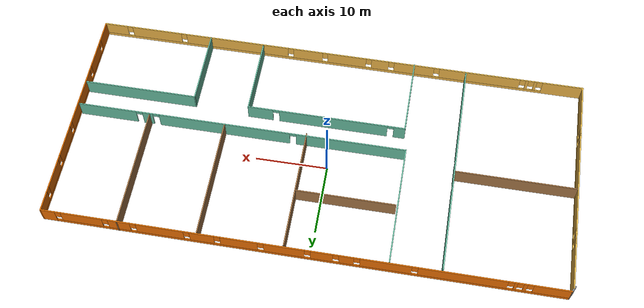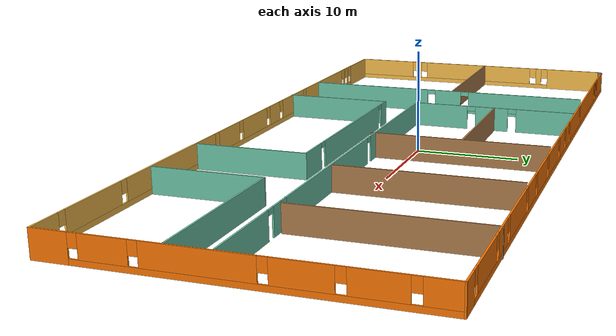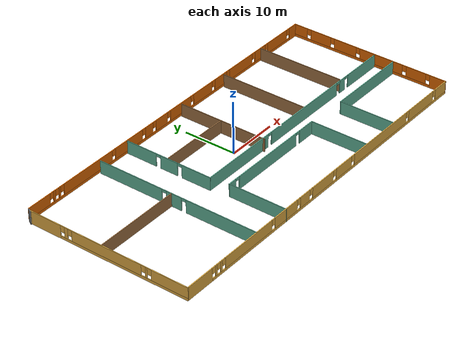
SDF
<?xml version='1.0'?>
<sdf version='1.6'>
  <model name='world'>
    <pose frame=''>0.997952 -1.93669 0 0 -0 0</pose>
    <link name='Wall_11'>
      <pose frame=''>-18.4502 -0.168882 0 0 0 -1.5708</pose>
      <visual name='Wall_11_Visual_0'>
        <pose frame=''>-9.3167 0 1.25 0 -0 0</pose>
        <geometry>
          <box>
            <size>12.8666 0.15 2.5</size>
          </box>
        </geometry>
        <material>
          <script>
            <uri>file://media/materials/scripts/gazebo.material</uri>
            <name>Gazebo/Grey</name>
          </script>
          <ambient>0.435294 0.796078 0.67451 1</ambient>
        </material>
        <meta>
          <layer>0</layer>
        </meta>
      </visual>
      <collision name='Wall_11_Collision_0'>
        <geometry>
          <box>
            <size>12.8666 0.15 2.5</size>
          </box>
        </geometry>
        <pose frame=''>-9.3167 0 1.25 0 -0 0</pose>
      </collision>
      <visual name='Wall_11_Visual_1'>
        <pose frame=''>-0.463393 0 1.25 0 -0 0</pose>
        <geometry>
          <box>
            <size>3.04002 0.15 2.5</size>
          </box>
        </geometry>
        <material>
          <script>
            <uri>file://media/materials/scripts/gazebo.material</uri>
            <name>Gazebo/Grey</name>
          </script>
          <ambient>0.435294 0.796078 0.67451 1</ambient>
        </material>
        <meta>
          <layer>0</layer>
        </meta>
      </visual>
      <collision name='Wall_11_Collision_1'>
        <geometry>
          <box>
            <size>3.04002 0.15 2.5</size>
          </box>
        </geometry>
        <pose frame=''>-0.463393 0 1.25 0 -0 0</pose>
      </collision>
      <visual name='Wall_11_Visual_2'>
        <pose frame=''>8.85331 0 1.25 0 -0 0</pose>
        <geometry>
          <box>
            <size>13.7934 0.15 2.5</size>
          </box>
        </geometry>
        <material>
          <script>
            <uri>file://media/materials/scripts/gazebo.material</uri>
            <name>Gazebo/Grey</name>
          </script>
          <ambient>0.435294 0.796078 0.67451 1</ambient>
        </material>
        <meta>
          <layer>0</layer>
        </meta>
      </visual>
      <collision name='Wall_11_Collision_2'>
        <geometry>
          <box>
            <size>13.7934 0.15 2.5</size>
          </box>
        </geometry>
        <pose frame=''>8.85331 0 1.25 0 -0 0</pose>
      </collision>
      <visual name='Wall_11_Visual_3'>
        <pose frame=''>-2.4334 0 2.25 0 -0 0</pose>
        <geometry>
          <box>
            <size>0.9 0.15 0.5</size>
          </box>
        </geometry>
        <material>
          <script>
            <uri>file://media/materials/scripts/gazebo.material</uri>
            <name>Gazebo/Grey</name>
          </script>
          <ambient>0.435294 0.796078 0.67451 1</ambient>
        </material>
        <meta>
          <layer>0</layer>
        </meta>
      </visual>
      <collision name='Wall_11_Collision_3'>
        <geometry>
          <box>
            <size>0.9 0.15 0.5</size>
          </box>
        </geometry>
        <pose frame=''>-2.4334 0 2.25 0 -0 0</pose>
      </collision>
      <visual name='Wall_11_Visual_4'>
        <pose frame=''>1.50662 0 2.25 0 -0 0</pose>
        <geometry>
          <box>
            <size>0.9 0.15 0.5</size>
          </box>
        </geometry>
        <material>
          <script>
            <uri>file://media/materials/scripts/gazebo.material</uri>
            <name>Gazebo/Grey</name>
          </script>
          <ambient>0.435294 0.796078 0.67451 1</ambient>
        </material>
        <meta>
          <layer>0</layer>
        </meta>
      </visual>
      <collision name='Wall_11_Collision_4'>
        <geometry>
          <box>
            <size>0.9 0.15 0.5</size>
          </box>
        </geometry>
        <pose frame=''>1.50662 0 2.25 0 -0 0</pose>
      </collision>
    </link>
    <link name='Wall_13'>
      <pose frame=''>-11.4716 7.14221 0 0 0 -1.5708</pose>
      <visual name='Wall_13_Visual_0'>
        <pose frame=''>-5.58135 0 1.25 0 -0 0</pose>
        <geometry>
          <box>
            <size>6.0873 0.15 2.5</size>
          </box>
        </geometry>
        <material>
          <script>
            <uri>file://media/materials/scripts/gazebo.material</uri>
            <name>Gazebo/Grey</name>
          </script>
          <ambient>0.435294 0.796078 0.67451 1</ambient>
        </material>
        <meta>
          <layer>0</layer>
        </meta>
      </visual>
      <collision name='Wall_13_Collision_0'>
        <geometry>
          <box>
            <size>6.0873 0.15 2.5</size>
          </box>
        </geometry>
        <pose frame=''>-5.58135 0 1.25 0 -0 0</pose>
      </collision>
      <visual name='Wall_13_Visual_1'>
        <pose frame=''>0.128558 0 1.25 0 -0 0</pose>
        <geometry>
          <box>
            <size>3.53252 0.15 2.5</size>
          </box>
        </geometry>
        <material>
          <script>
            <uri>file://media/materials/scripts/gazebo.material</uri>
            <name>Gazebo/Grey</name>
          </script>
          <ambient>0.435294 0.796078 0.67451 1</ambient>
        </material>
        <meta>
          <layer>0</layer>
        </meta>
      </visual>
      <collision name='Wall_13_Collision_1'>
        <geometry>
          <box>
            <size>3.53252 0.15 2.5</size>
          </box>
        </geometry>
        <pose frame=''>0.128558 0 1.25 0 -0 0</pose>
      </collision>
      <visual name='Wall_13_Visual_2'>
        <pose frame=''>5.70991 0 1.25 0 -0 0</pose>
        <geometry>
          <box>
            <size>5.83018 0.15 2.5</size>
          </box>
        </geometry>
        <material>
          <script>
            <uri>file://media/materials/scripts/gazebo.material</uri>
            <name>Gazebo/Grey</name>
          </script>
          <ambient>0.435294 0.796078 0.67451 1</ambient>
        </material>
        <meta>
          <layer>0</layer>
        </meta>
      </visual>
      <collision name='Wall_13_Collision_2'>
        <geometry>
          <box>
            <size>5.83018 0.15 2.5</size>
          </box>
        </geometry>
        <pose frame=''>5.70991 0 1.25 0 -0 0</pose>
      </collision>
      <visual name='Wall_13_Visual_3'>
        <pose frame=''>-2.0877 0 2.25 0 -0 0</pose>
        <geometry>
          <box>
            <size>0.9 0.15 0.5</size>
          </box>
        </geometry>
        <material>
          <script>
            <uri>file://media/materials/scripts/gazebo.material</uri>
            <name>Gazebo/Grey</name>
          </script>
          <ambient>0.435294 0.796078 0.67451 1</ambient>
        </material>
        <meta>
          <layer>0</layer>
        </meta>
      </visual>
      <collision name='Wall_13_Collision_3'>
        <geometry>
          <box>
            <size>0.9 0.15 0.5</size>
          </box>
        </geometry>
        <pose frame=''>-2.0877 0 2.25 0 -0 0</pose>
      </collision>
      <visual name='Wall_13_Visual_4'>
        <pose frame=''>2.34482 0 2.25 0 -0 0</pose>
        <geometry>
          <box>
            <size>0.9 0.15 0.5</size>
          </box>
        </geometry>
        <material>
          <script>
            <uri>file://media/materials/scripts/gazebo.material</uri>
            <name>Gazebo/Grey</name>
          </script>
          <ambient>0.435294 0.796078 0.67451 1</ambient>
        </material>
        <meta>
          <layer>0</layer>
        </meta>
      </visual>
      <collision name='Wall_13_Collision_4'>
        <geometry>
          <box>
            <size>0.9 0.15 0.5</size>
          </box>
        </geometry>
        <pose frame=''>2.34482 0 2.25 0 -0 0</pose>
      </collision>
    </link>
    <link name='Wall_14'>
      <pose frame=''>11.8284 -1.40779 0 0 -0 0</pose>
      <visual name='Wall_14_Visual_0'>
        <pose frame=''>-15.6414 0 1.25 0 -0 0</pose>
        <geometry>
          <box>
            <size>15.4671 0.15 2.5</size>
          </box>
        </geometry>
        <material>
          <script>
            <uri>file://media/materials/scripts/gazebo.material</uri>
            <name>Gazebo/Grey</name>
          </script>
          <ambient>0.435294 0.796078 0.67451 1</ambient>
        </material>
        <meta>
          <layer>0</layer>
        </meta>
      </visual>
      <collision name='Wall_14_Collision_0'>
        <geometry>
          <box>
            <size>15.4671 0.15 2.5</size>
          </box>
        </geometry>
        <pose frame=''>-15.6414 0 1.25 0 -0 0</pose>
      </collision>
      <visual name='Wall_14_Visual_1'>
        <pose frame=''>2.37266 0 1.25 0 -0 0</pose>
        <geometry>
          <box>
            <size>18.761 0.15 2.5</size>
          </box>
        </geometry>
        <material>
          <script>
            <uri>file://media/materials/scripts/gazebo.material</uri>
            <name>Gazebo/Grey</name>
          </script>
          <ambient>0.435294 0.796078 0.67451 1</ambient>
        </material>
        <meta>
          <layer>0</layer>
        </meta>
      </visual>
      <collision name='Wall_14_Collision_1'>
        <geometry>
          <box>
            <size>18.761 0.15 2.5</size>
          </box>
        </geometry>
        <pose frame=''>2.37266 0 1.25 0 -0 0</pose>
      </collision>
      <visual name='Wall_14_Visual_2'>
        <pose frame=''>13.406 0 1.25 0 -0 0</pose>
        <geometry>
          <box>
            <size>1.50558 0.15 2.5</size>
          </box>
        </geometry>
        <material>
          <script>
            <uri>file://media/materials/scripts/gazebo.material</uri>
            <name>Gazebo/Grey</name>
          </script>
          <ambient>0.435294 0.796078 0.67451 1</ambient>
        </material>
        <meta>
          <layer>0</layer>
        </meta>
      </visual>
      <collision name='Wall_14_Collision_2'>
        <geometry>
          <box>
            <size>1.50558 0.15 2.5</size>
          </box>
        </geometry>
        <pose frame=''>13.406 0 1.25 0 -0 0</pose>
      </collision>
      <visual name='Wall_14_Visual_3'>
        <pose frame=''>19.2169 0 1.25 0 -0 0</pose>
        <geometry>
          <box>
            <size>8.31625 0.15 2.5</size>
          </box>
        </geometry>
        <material>
          <script>
            <uri>file://media/materials/scripts/gazebo.material</uri>
            <name>Gazebo/Grey</name>
          </script>
          <ambient>0.435294 0.796078 0.67451 1</ambient>
        </material>
        <meta>
          <layer>0</layer>
        </meta>
      </visual>
      <collision name='Wall_14_Collision_3'>
        <geometry>
          <box>
            <size>8.31625 0.15 2.5</size>
          </box>
        </geometry>
        <pose frame=''>19.2169 0 1.25 0 -0 0</pose>
      </collision>
      <visual name='Wall_14_Visual_4'>
        <pose frame=''>-7.45785 0 2.25 0 -0 0</pose>
        <geometry>
          <box>
            <size>0.9 0.15 0.5</size>
          </box>
        </geometry>
        <material>
          <script>
            <uri>file://media/materials/scripts/gazebo.material</uri>
            <name>Gazebo/Grey</name>
          </script>
          <ambient>0.435294 0.796078 0.67451 1</ambient>
        </material>
        <meta>
          <layer>0</layer>
        </meta>
      </visual>
      <collision name='Wall_14_Collision_4'>
        <geometry>
          <box>
            <size>0.9 0.15 0.5</size>
          </box>
        </geometry>
        <pose frame=''>-7.45785 0 2.25 0 -0 0</pose>
      </collision>
      <visual name='Wall_14_Visual_5'>
        <pose frame=''>12.2032 0 2.25 0 -0 0</pose>
        <geometry>
          <box>
            <size>0.9 0.15 0.5</size>
          </box>
        </geometry>
        <material>
          <script>
            <uri>file://media/materials/scripts/gazebo.material</uri>
            <name>Gazebo/Grey</name>
          </script>
          <ambient>0.435294 0.796078 0.67451 1</ambient>
        </material>
        <meta>
          <layer>0</layer>
        </meta>
      </visual>
      <collision name='Wall_14_Collision_5'>
        <geometry>
          <box>
            <size>0.9 0.15 0.5</size>
          </box>
        </geometry>
        <pose frame=''>12.2032 0 2.25 0 -0 0</pose>
      </collision>
      <visual name='Wall_14_Visual_6'>
        <pose frame=''>14.6087 0 2.25 0 -0 0</pose>
        <geometry>
          <box>
            <size>0.9 0.15 0.5</size>
          </box>
        </geometry>
        <material>
          <script>
            <uri>file://media/materials/scripts/gazebo.material</uri>
            <name>Gazebo/Grey</name>
          </script>
          <ambient>0.435294 0.796078 0.67451 1</ambient>
        </material>
        <meta>
          <layer>0</layer>
        </meta>
      </visual>
      <collision name='Wall_14_Collision_6'>
        <geometry>
          <box>
            <size>0.9 0.15 0.5</size>
          </box>
        </geometry>
        <pose frame=''>14.6087 0 2.25 0 -0 0</pose>
      </collision>
    </link>
    <link name='Wall_16'>
      <collision name='Wall_16_Collision'>
        <geometry>
          <box>
            <size>17.5 0.15 2.5</size>
          </box>
        </geometry>
        <pose frame=''>0 0 1.25 0 -0 0</pose>
      </collision>
      <visual name='Wall_16_Visual'>
        <pose frame=''>0 0 1.25 0 -0 0</pose>
        <geometry>
          <box>
            <size>17.5 0.15 2.5</size>
          </box>
        </geometry>
        <material>
          <script>
            <uri>file://media/materials/scripts/gazebo.material</uri>
            <name>Gazebo/Wood</name>
          </script>
          <ambient>1 1 1 1</ambient>
        </material>
        <meta>
          <layer>0</layer>
        </meta>
      </visual>
      <pose frame=''>2.48559 6.92417 0 0 0 -1.5708</pose>
    </link>
    <link name='Wall_18'>
      <collision name='Wall_18_Collision'>
        <geometry>
          <box>
            <size>17 0.15 2.5</size>
          </box>
        </geometry>
        <pose frame=''>0 0 1.25 0 -0 0</pose>
      </collision>
      <visual name='Wall_18_Visual'>
        <pose frame=''>0 0 1.25 0 -0 0</pose>
        <geometry>
          <box>
            <size>17 0.15 2.5</size>
          </box>
        </geometry>
        <material>
          <script>
            <uri>file://media/materials/scripts/gazebo.material</uri>
            <name>Gazebo/Wood</name>
          </script>
          <ambient>1 1 1 1</ambient>
        </material>
        <meta>
          <layer>0</layer>
        </meta>
      </visual>
      <pose frame=''>14.1166 7.17417 0 0 0 -1.5708</pose>
    </link>
    <link name='Wall_20'>
      <collision name='Wall_20_Collision'>
        <geometry>
          <box>
            <size>17.25 0.15 2.5</size>
          </box>
        </geometry>
        <pose frame=''>0 0 1.25 0 -0 0</pose>
      </collision>
      <visual name='Wall_20_Visual'>
        <pose frame=''>0 0 1.25 0 -0 0</pose>
        <geometry>
          <box>
            <size>17.25 0.15 2.5</size>
          </box>
        </geometry>
        <material>
          <script>
            <uri>file://media/materials/scripts/gazebo.material</uri>
            <name>Gazebo/Wood</name>
          </script>
          <ambient>1 1 1 1</ambient>
        </material>
        <meta>
          <layer>0</layer>
        </meta>
      </visual>
      <pose frame=''>24.9101 7.42136 0 0 0 -1.5708</pose>
    </link>
    <link name='Wall_22'>
      <collision name='Wall_22_Collision'>
        <geometry>
          <box>
            <size>13.75 0.15 2.5</size>
          </box>
        </geometry>
        <pose frame=''>0 0 1.25 0 -0 0</pose>
      </collision>
      <visual name='Wall_22_Visual'>
        <pose frame=''>0 0 1.25 0 -0 0</pose>
        <geometry>
          <box>
            <size>13.75 0.15 2.5</size>
          </box>
        </geometry>
        <material>
          <script>
            <uri>file://media/materials/scripts/gazebo.material</uri>
            <name>Gazebo/Wood</name>
          </script>
          <ambient>1 1 1 1</ambient>
        </material>
        <meta>
          <layer>0</layer>
        </meta>
      </visual>
      <pose frame=''>-4.39243 7.31791 0 0 -0 0</pose>
    </link>
    <link name='Wall_24'>
      <collision name='Wall_24_Collision'>
        <geometry>
          <box>
            <size>11.25 0.15 2.5</size>
          </box>
        </geometry>
        <pose frame=''>0 0 1.25 0 -0 0</pose>
      </collision>
      <visual name='Wall_24_Visual'>
        <pose frame=''>0 0 1.25 0 -0 0</pose>
        <geometry>
          <box>
            <size>11.25 0.15 2.5</size>
          </box>
        </geometry>
        <material>
          <script>
            <uri>file://media/materials/scripts/gazebo.material</uri>
            <name>Gazebo/Grey</name>
          </script>
          <ambient>0.435294 0.796078 0.67451 1</ambient>
        </material>
        <meta>
          <layer>0</layer>
        </meta>
      </visual>
      <pose frame=''>-10.9133 -10.4214 0 0 0 -1.5708</pose>
    </link>
    <link name='Wall_26'>
      <pose frame=''>0.261708 -4.87136 0 0 -0 0</pose>
      <visual name='Wall_26_Visual_0'>
        <pose frame=''>-10.4274 0 1.25 0 -0 0</pose>
        <geometry>
          <box>
            <size>1.64525 0.15 2.5</size>
          </box>
        </geometry>
        <material>
          <script>
            <uri>file://media/materials/scripts/gazebo.material</uri>
            <name>Gazebo/Grey</name>
          </script>
          <ambient>0.435294 0.796078 0.67451 1</ambient>
        </material>
        <meta>
          <layer>0</layer>
        </meta>
      </visual>
      <collision name='Wall_26_Collision_0'>
        <geometry>
          <box>
            <size>1.64525 0.15 2.5</size>
          </box>
        </geometry>
        <pose frame=''>-10.4274 0 1.25 0 -0 0</pose>
      </collision>
      <visual name='Wall_26_Visual_1'>
        <pose frame=''>-0.993281 0 1.25 0 -0 0</pose>
        <geometry>
          <box>
            <size>15.4229 0.15 2.5</size>
          </box>
        </geometry>
        <material>
          <script>
            <uri>file://media/materials/scripts/gazebo.material</uri>
            <name>Gazebo/Grey</name>
          </script>
          <ambient>0.435294 0.796078 0.67451 1</ambient>
        </material>
        <meta>
          <layer>0</layer>
        </meta>
      </visual>
      <collision name='Wall_26_Collision_1'>
        <geometry>
          <box>
            <size>15.4229 0.15 2.5</size>
          </box>
        </geometry>
        <pose frame=''>-0.993281 0 1.25 0 -0 0</pose>
      </collision>
      <visual name='Wall_26_Visual_2'>
        <pose frame=''>9.4341 0 1.25 0 -0 0</pose>
        <geometry>
          <box>
            <size>3.63181 0.15 2.5</size>
          </box>
        </geometry>
        <material>
          <script>
            <uri>file://media/materials/scripts/gazebo.material</uri>
            <name>Gazebo/Grey</name>
          </script>
          <ambient>0.435294 0.796078 0.67451 1</ambient>
        </material>
        <meta>
          <layer>0</layer>
        </meta>
      </visual>
      <collision name='Wall_26_Collision_2'>
        <geometry>
          <box>
            <size>3.63181 0.15 2.5</size>
          </box>
        </geometry>
        <pose frame=''>9.4341 0 1.25 0 -0 0</pose>
      </collision>
      <visual name='Wall_26_Visual_3'>
        <pose frame=''>-9.15475 0 2.25 0 -0 0</pose>
        <geometry>
          <box>
            <size>0.9 0.15 0.5</size>
          </box>
        </geometry>
        <material>
          <script>
            <uri>file://media/materials/scripts/gazebo.material</uri>
            <name>Gazebo/Grey</name>
          </script>
          <ambient>0.435294 0.796078 0.67451 1</ambient>
        </material>
        <meta>
          <layer>0</layer>
        </meta>
      </visual>
      <collision name='Wall_26_Collision_3'>
        <geometry>
          <box>
            <size>0.9 0.15 0.5</size>
          </box>
        </geometry>
        <pose frame=''>-9.15475 0 2.25 0 -0 0</pose>
      </collision>
      <visual name='Wall_26_Visual_4'>
        <pose frame=''>7.16819 0 2.25 0 -0 0</pose>
        <geometry>
          <box>
            <size>0.9 0.15 0.5</size>
          </box>
        </geometry>
        <material>
          <script>
            <uri>file://media/materials/scripts/gazebo.material</uri>
            <name>Gazebo/Grey</name>
          </script>
          <ambient>0.435294 0.796078 0.67451 1</ambient>
        </material>
        <meta>
          <layer>0</layer>
        </meta>
      </visual>
      <collision name='Wall_26_Collision_4'>
        <geometry>
          <box>
            <size>0.9 0.15 0.5</size>
          </box>
        </geometry>
        <pose frame=''>7.16819 0 2.25 0 -0 0</pose>
      </collision>
    </link>
    <link name='Wall_27'>
      <collision name='Wall_27_Collision'>
        <geometry>
          <box>
            <size>11 0.15 2.5</size>
          </box>
        </geometry>
        <pose frame=''>0 0 1.25 0 -0 0</pose>
      </collision>
      <visual name='Wall_27_Visual'>
        <pose frame=''>0 0 1.25 0 -0 0</pose>
        <geometry>
          <box>
            <size>11 0.15 2.5</size>
          </box>
        </geometry>
        <material>
          <script>
            <uri>file://media/materials/scripts/gazebo.material</uri>
            <name>Gazebo/Grey</name>
          </script>
          <ambient>0.435294 0.796078 0.67451 1</ambient>
        </material>
        <meta>
          <layer>0</layer>
        </meta>
      </visual>
      <pose frame=''>11.4367 -10.2964 0 0 0 -1.5708</pose>
    </link>
    <link name='Wall_29'>
      <collision name='Wall_29_Collision'>
        <geometry>
          <box>
            <size>16 0.15 2.5</size>
          </box>
        </geometry>
        <pose frame=''>0 0 1.25 0 -0 0</pose>
      </collision>
      <visual name='Wall_29_Visual'>
        <pose frame=''>0 0 1.25 0 -0 0</pose>
        <geometry>
          <box>
            <size>16 0.15 2.5</size>
          </box>
        </geometry>
        <material>
          <script>
            <uri>file://media/materials/scripts/gazebo.material</uri>
            <name>Gazebo/Grey</name>
          </script>
          <ambient>0.435294 0.796078 0.67451 1</ambient>
        </material>
        <meta>
          <layer>0</layer>
        </meta>
      </visual>
      <pose frame=''>27.2523 -5.24355 0 0 -0 0</pose>
    </link>
    <link name='Wall_32'>
      <collision name='Wall_32_Collision'>
        <geometry>
          <box>
            <size>10.75 0.15 2.5</size>
          </box>
        </geometry>
        <pose frame=''>0 0 1.25 0 -0 0</pose>
      </collision>
      <visual name='Wall_32_Visual'>
        <pose frame=''>0 0 1.25 0 -0 0</pose>
        <geometry>
          <box>
            <size>10.75 0.15 2.5</size>
          </box>
        </geometry>
        <material>
          <script>
            <uri>file://media/materials/scripts/gazebo.material</uri>
            <name>Gazebo/Grey</name>
          </script>
          <ambient>0.435294 0.796078 0.67451 1</ambient>
        </material>
        <meta>
          <layer>0</layer>
        </meta>
      </visual>
      <pose frame=''>19.3273 -10.5435 0 0 0 -1.5708</pose>
    </link>
    <link name='Wall_34'>
      <collision name='Wall_34_Collision'>
        <geometry>
          <box>
            <size>16.75 0.15 2.5</size>
          </box>
        </geometry>
        <pose frame=''>0 0 1.25 0 -0 0</pose>
      </collision>
      <visual name='Wall_34_Visual'>
        <pose frame=''>0 0 1.25 0 -0 0</pose>
        <geometry>
          <box>
            <size>16.75 0.15 2.5</size>
          </box>
        </geometry>
        <material>
          <script>
            <uri>file://media/materials/scripts/gazebo.material</uri>
            <name>Gazebo/Wood</name>
          </script>
          <ambient>1 1 1 1</ambient>
        </material>
        <meta>
          <layer>0</layer>
        </meta>
      </visual>
      <pose frame=''>-26.8057 0.804561 0 0 -0 0</pose>
    </link>
    <link name='Wall_5'>
      <pose frame=''>-35.1988 -0.26193 0 0 0 -1.5708</pose>
      <visual name='Wall_5_Visual_0'>
        <pose frame=''>-12.5335 0 1.25 0 -0 0</pose>
        <geometry>
          <box>
            <size>6.43309 0.15 2.5</size>
          </box>
        </geometry>
        <material>
          <script>
            <uri>file://media/materials/scripts/gazebo.material</uri>
            <name>Gazebo/Grey</name>
          </script>
          <ambient>1 0.764706 0.305882 1</ambient>
        </material>
        <meta>
          <layer>0</layer>
        </meta>
      </visual>
      <collision name='Wall_5_Collision_0'>
        <geometry>
          <box>
            <size>6.43309 0.15 2.5</size>
          </box>
        </geometry>
        <pose frame=''>-12.5335 0 1.25 0 -0 0</pose>
      </collision>
      <visual name='Wall_5_Visual_1'>
        <pose frame=''>3.21654 0 0.25 0 -0 0</pose>
        <geometry>
          <box>
            <size>25.0669 0.15 0.5</size>
          </box>
        </geometry>
        <material>
          <script>
            <uri>file://media/materials/scripts/gazebo.material</uri>
            <name>Gazebo/Grey</name>
          </script>
          <ambient>1 0.764706 0.305882 1</ambient>
        </material>
        <meta>
          <layer>0</layer>
        </meta>
      </visual>
      <collision name='Wall_5_Collision_1'>
        <geometry>
          <box>
            <size>25.0669 0.15 0.5</size>
          </box>
        </geometry>
        <pose frame=''>3.21654 0 0.25 0 -0 0</pose>
      </collision>
      <visual name='Wall_5_Visual_2'>
        <pose frame=''>-8.17816 0 1.5 0 -0 0</pose>
        <geometry>
          <box>
            <size>0.677508 0.15 2</size>
          </box>
        </geometry>
        <material>
          <script>
            <uri>file://media/materials/scripts/gazebo.material</uri>
            <name>Gazebo/Grey</name>
          </script>
          <ambient>1 0.764706 0.305882 1</ambient>
        </material>
        <meta>
          <layer>0</layer>
        </meta>
      </visual>
      <collision name='Wall_5_Collision_2'>
        <geometry>
          <box>
            <size>0.677508 0.15 2</size>
          </box>
        </geometry>
        <pose frame=''>-8.17816 0 1.5 0 -0 0</pose>
      </collision>
      <visual name='Wall_5_Visual_3'>
        <pose frame=''>-0.127812 0 1.5 0 -0 0</pose>
        <geometry>
          <box>
            <size>13.8232 0.15 2</size>
          </box>
        </geometry>
        <material>
          <script>
            <uri>file://media/materials/scripts/gazebo.material</uri>
            <name>Gazebo/Grey</name>
          </script>
          <ambient>1 0.764706 0.305882 1</ambient>
        </material>
        <meta>
          <layer>0</layer>
        </meta>
      </visual>
      <collision name='Wall_5_Collision_3'>
        <geometry>
          <box>
            <size>13.8232 0.15 2</size>
          </box>
        </geometry>
        <pose frame=''>-0.127812 0 1.5 0 -0 0</pose>
      </collision>
      <visual name='Wall_5_Visual_4'>
        <pose frame=''>7.76499 0 1.5 0 -0 0</pose>
        <geometry>
          <box>
            <size>0.362429 0.15 2</size>
          </box>
        </geometry>
        <material>
          <script>
            <uri>file://media/materials/scripts/gazebo.material</uri>
            <name>Gazebo/Grey</name>
          </script>
          <ambient>1 0.764706 0.305882 1</ambient>
        </material>
        <meta>
          <layer>0</layer>
        </meta>
      </visual>
      <collision name='Wall_5_Collision_4'>
        <geometry>
          <box>
            <size>0.362429 0.15 2</size>
          </box>
        </geometry>
        <pose frame=''>7.76499 0 1.5 0 -0 0</pose>
      </collision>
      <visual name='Wall_5_Visual_5'>
        <pose frame=''>12.2481 0 1.5 0 -0 0</pose>
        <geometry>
          <box>
            <size>7.00379 0.15 2</size>
          </box>
        </geometry>
        <material>
          <script>
            <uri>file://media/materials/scripts/gazebo.material</uri>
            <name>Gazebo/Grey</name>
          </script>
          <ambient>1 0.764706 0.305882 1</ambient>
        </material>
        <meta>
          <layer>0</layer>
        </meta>
      </visual>
      <collision name='Wall_5_Collision_5'>
        <geometry>
          <box>
            <size>7.00379 0.15 2</size>
          </box>
        </geometry>
        <pose frame=''>12.2481 0 1.5 0 -0 0</pose>
      </collision>
      <visual name='Wall_5_Visual_6'>
        <pose frame=''>-8.91691 0 1.9 0 -0 0</pose>
        <geometry>
          <box>
            <size>0.8 0.15 1.2</size>
          </box>
        </geometry>
        <material>
          <script>
            <uri>file://media/materials/scripts/gazebo.material</uri>
            <name>Gazebo/Grey</name>
          </script>
          <ambient>1 0.764706 0.305882 1</ambient>
        </material>
        <meta>
          <layer>0</layer>
        </meta>
      </visual>
      <collision name='Wall_5_Collision_6'>
        <geometry>
          <box>
            <size>0.8 0.15 1.2</size>
          </box>
        </geometry>
        <pose frame=''>-8.91691 0 1.9 0 -0 0</pose>
      </collision>
      <visual name='Wall_5_Visual_7'>
        <pose frame=''>-7.4394 0 1.9 0 -0 0</pose>
        <geometry>
          <box>
            <size>0.8 0.15 1.2</size>
          </box>
        </geometry>
        <material>
          <script>
            <uri>file://media/materials/scripts/gazebo.material</uri>
            <name>Gazebo/Grey</name>
          </script>
          <ambient>1 0.764706 0.305882 1</ambient>
        </material>
        <meta>
          <layer>0</layer>
        </meta>
      </visual>
      <collision name='Wall_5_Collision_7'>
        <geometry>
          <box>
            <size>0.8 0.15 1.2</size>
          </box>
        </geometry>
        <pose frame=''>-7.4394 0 1.9 0 -0 0</pose>
      </collision>
      <visual name='Wall_5_Visual_8'>
        <pose frame=''>7.18378 0 1.9 0 -0 0</pose>
        <geometry>
          <box>
            <size>0.8 0.15 1.2</size>
          </box>
        </geometry>
        <material>
          <script>
            <uri>file://media/materials/scripts/gazebo.material</uri>
            <name>Gazebo/Grey</name>
          </script>
          <ambient>1 0.764706 0.305882 1</ambient>
        </material>
        <meta>
          <layer>0</layer>
        </meta>
      </visual>
      <collision name='Wall_5_Collision_8'>
        <geometry>
          <box>
            <size>0.8 0.15 1.2</size>
          </box>
        </geometry>
        <pose frame=''>7.18378 0 1.9 0 -0 0</pose>
      </collision>
      <visual name='Wall_5_Visual_9'>
        <pose frame=''>8.34621 0 1.9 0 -0 0</pose>
        <geometry>
          <box>
            <size>0.8 0.15 1.2</size>
          </box>
        </geometry>
        <material>
          <script>
            <uri>file://media/materials/scripts/gazebo.material</uri>
            <name>Gazebo/Grey</name>
          </script>
          <ambient>1 0.764706 0.305882 1</ambient>
        </material>
        <meta>
          <layer>0</layer>
        </meta>
      </visual>
      <collision name='Wall_5_Collision_9'>
        <geometry>
          <box>
            <size>0.8 0.15 1.2</size>
          </box>
        </geometry>
        <pose frame=''>8.34621 0 1.9 0 -0 0</pose>
      </collision>
    </link>
    <link name='Wall_6'>
      <pose frame=''>0.101225 -15.9369 0 0 -0 0</pose>
      <visual name='Wall_6_Visual_0'>
        <pose frame=''>-32.4811 0 1.25 0 -0 0</pose>
        <geometry>
          <box>
            <size>5.78775 0.15 2.5</size>
          </box>
        </geometry>
        <material>
          <script>
            <uri>file://media/materials/scripts/gazebo.material</uri>
            <name>Gazebo/Grey</name>
          </script>
          <ambient>1 0.764706 0.305882 1</ambient>
        </material>
        <meta>
          <layer>0</layer>
        </meta>
      </visual>
      <collision name='Wall_6_Collision_0'>
        <geometry>
          <box>
            <size>5.78775 0.15 2.5</size>
          </box>
        </geometry>
        <pose frame=''>-32.4811 0 1.25 0 -0 0</pose>
      </collision>
      <visual name='Wall_6_Visual_1'>
        <pose frame=''>2.89388 0 0.25 0 -0 0</pose>
        <geometry>
          <box>
            <size>64.9622 0.15 0.5</size>
          </box>
        </geometry>
        <material>
          <script>
            <uri>file://media/materials/scripts/gazebo.material</uri>
            <name>Gazebo/Grey</name>
          </script>
          <ambient>1 0.764706 0.305882 1</ambient>
        </material>
        <meta>
          <layer>0</layer>
        </meta>
      </visual>
      <collision name='Wall_6_Collision_1'>
        <geometry>
          <box>
            <size>64.9622 0.15 0.5</size>
          </box>
        </geometry>
        <pose frame=''>2.89388 0 0.25 0 -0 0</pose>
      </collision>
      <visual name='Wall_6_Visual_2'>
        <pose frame=''>-28.5804 0 1.5 0 -0 0</pose>
        <geometry>
          <box>
            <size>0.413667 0.15 2</size>
          </box>
        </geometry>
        <material>
          <script>
            <uri>file://media/materials/scripts/gazebo.material</uri>
            <name>Gazebo/Grey</name>
          </script>
          <ambient>1 0.764706 0.305882 1</ambient>
        </material>
        <meta>
          <layer>0</layer>
        </meta>
      </visual>
      <collision name='Wall_6_Collision_2'>
        <geometry>
          <box>
            <size>0.413667 0.15 2</size>
          </box>
        </geometry>
        <pose frame=''>-28.5804 0 1.5 0 -0 0</pose>
      </collision>
      <visual name='Wall_6_Visual_3'>
        <pose frame=''>-27.3667 0 1.5 0 -0 0</pose>
        <geometry>
          <box>
            <size>0.413667 0.15 2</size>
          </box>
        </geometry>
        <material>
          <script>
            <uri>file://media/materials/scripts/gazebo.material</uri>
            <name>Gazebo/Grey</name>
          </script>
          <ambient>1 0.764706 0.305882 1</ambient>
        </material>
        <meta>
          <layer>0</layer>
        </meta>
      </visual>
      <collision name='Wall_6_Collision_3'>
        <geometry>
          <box>
            <size>0.413667 0.15 2</size>
          </box>
        </geometry>
        <pose frame=''>-27.3667 0 1.5 0 -0 0</pose>
      </collision>
      <visual name='Wall_6_Visual_4'>
        <pose frame=''>-20.5298 0 1.5 0 -0 0</pose>
        <geometry>
          <box>
            <size>11.6603 0.15 2</size>
          </box>
        </geometry>
        <material>
          <script>
            <uri>file://media/materials/scripts/gazebo.material</uri>
            <name>Gazebo/Grey</name>
          </script>
          <ambient>1 0.764706 0.305882 1</ambient>
        </material>
        <meta>
          <layer>0</layer>
        </meta>
      </visual>
      <collision name='Wall_6_Collision_4'>
        <geometry>
          <box>
            <size>11.6603 0.15 2</size>
          </box>
        </geometry>
        <pose frame=''>-20.5298 0 1.5 0 -0 0</pose>
      </collision>
      <visual name='Wall_6_Visual_5'>
        <pose frame=''>-10.9822 0 1.5 0 -0 0</pose>
        <geometry>
          <box>
            <size>5.83472 0.15 2</size>
          </box>
        </geometry>
        <material>
          <script>
            <uri>file://media/materials/scripts/gazebo.material</uri>
            <name>Gazebo/Grey</name>
          </script>
          <ambient>1 0.764706 0.305882 1</ambient>
        </material>
        <meta>
          <layer>0</layer>
        </meta>
      </visual>
      <collision name='Wall_6_Collision_5'>
        <geometry>
          <box>
            <size>5.83472 0.15 2</size>
          </box>
        </geometry>
        <pose frame=''>-10.9822 0 1.5 0 -0 0</pose>
      </collision>
      <visual name='Wall_6_Visual_6'>
        <pose frame=''>-5.99726 0 1.5 0 -0 0</pose>
        <geometry>
          <box>
            <size>2.53524 0.15 2</size>
          </box>
        </geometry>
        <material>
          <script>
            <uri>file://media/materials/scripts/gazebo.material</uri>
            <name>Gazebo/Grey</name>
          </script>
          <ambient>1 0.764706 0.305882 1</ambient>
        </material>
        <meta>
          <layer>0</layer>
        </meta>
      </visual>
      <collision name='Wall_6_Collision_6'>
        <geometry>
          <box>
            <size>2.53524 0.15 2</size>
          </box>
        </geometry>
        <pose frame=''>-5.99726 0 1.5 0 -0 0</pose>
      </collision>
      <visual name='Wall_6_Visual_7'>
        <pose frame=''>-1.09549 0 1.5 0 -0 0</pose>
        <geometry>
          <box>
            <size>5.66831 0.15 2</size>
          </box>
        </geometry>
        <material>
          <script>
            <uri>file://media/materials/scripts/gazebo.material</uri>
            <name>Gazebo/Grey</name>
          </script>
          <ambient>1 0.764706 0.305882 1</ambient>
        </material>
        <meta>
          <layer>0</layer>
        </meta>
      </visual>
      <collision name='Wall_6_Collision_7'>
        <geometry>
          <box>
            <size>5.66831 0.15 2</size>
          </box>
        </geometry>
        <pose frame=''>-1.09549 0 1.5 0 -0 0</pose>
      </collision>
      <visual name='Wall_6_Visual_8'>
        <pose frame=''>4.69748 0 1.5 0 -0 0</pose>
        <geometry>
          <box>
            <size>4.31763 0.15 2</size>
          </box>
        </geometry>
        <material>
          <script>
            <uri>file://media/materials/scripts/gazebo.material</uri>
            <name>Gazebo/Grey</name>
          </script>
          <ambient>1 0.764706 0.305882 1</ambient>
        </material>
        <meta>
          <layer>0</layer>
        </meta>
      </visual>
      <collision name='Wall_6_Collision_8'>
        <geometry>
          <box>
            <size>4.31763 0.15 2</size>
          </box>
        </geometry>
        <pose frame=''>4.69748 0 1.5 0 -0 0</pose>
      </collision>
      <visual name='Wall_6_Visual_9'>
        <pose frame=''>15.3167 0 1.5 0 -0 0</pose>
        <geometry>
          <box>
            <size>15.3208 0.15 2</size>
          </box>
        </geometry>
        <material>
          <script>
            <uri>file://media/materials/scripts/gazebo.material</uri>
            <name>Gazebo/Grey</name>
          </script>
          <ambient>1 0.764706 0.305882 1</ambient>
        </material>
        <meta>
          <layer>0</layer>
        </meta>
      </visual>
      <collision name='Wall_6_Collision_9'>
        <geometry>
          <box>
            <size>15.3208 0.15 2</size>
          </box>
        </geometry>
        <pose frame=''>15.3167 0 1.5 0 -0 0</pose>
      </collision>
      <visual name='Wall_6_Visual_10'>
        <pose frame=''>27.4964 0 1.5 0 -0 0</pose>
        <geometry>
          <box>
            <size>7.43877 0.15 2</size>
          </box>
        </geometry>
        <material>
          <script>
            <uri>file://media/materials/scripts/gazebo.material</uri>
            <name>Gazebo/Grey</name>
          </script>
          <ambient>1 0.764706 0.305882 1</ambient>
        </material>
        <meta>
          <layer>0</layer>
        </meta>
      </visual>
      <collision name='Wall_6_Collision_10'>
        <geometry>
          <box>
            <size>7.43877 0.15 2</size>
          </box>
        </geometry>
        <pose frame=''>27.4964 0 1.5 0 -0 0</pose>
      </collision>
      <visual name='Wall_6_Visual_11'>
        <pose frame=''>33.6954 0 1.5 0 -0 0</pose>
        <geometry>
          <box>
            <size>3.35917 0.15 2</size>
          </box>
        </geometry>
        <material>
          <script>
            <uri>file://media/materials/scripts/gazebo.material</uri>
            <name>Gazebo/Grey</name>
          </script>
          <ambient>1 0.764706 0.305882 1</ambient>
        </material>
        <meta>
          <layer>0</layer>
        </meta>
      </visual>
      <collision name='Wall_6_Collision_11'>
        <geometry>
          <box>
            <size>3.35917 0.15 2</size>
          </box>
        </geometry>
        <pose frame=''>33.6954 0 1.5 0 -0 0</pose>
      </collision>
      <visual name='Wall_6_Visual_12'>
        <pose frame=''>-29.1872 0 1.9 0 -0 0</pose>
        <geometry>
          <box>
            <size>0.8 0.15 1.2</size>
          </box>
        </geometry>
        <material>
          <script>
            <uri>file://media/materials/scripts/gazebo.material</uri>
            <name>Gazebo/Grey</name>
          </script>
          <ambient>1 0.764706 0.305882 1</ambient>
        </material>
        <meta>
          <layer>0</layer>
        </meta>
      </visual>
      <collision name='Wall_6_Collision_12'>
        <geometry>
          <box>
            <size>0.8 0.15 1.2</size>
          </box>
        </geometry>
        <pose frame=''>-29.1872 0 1.9 0 -0 0</pose>
      </collision>
      <visual name='Wall_6_Visual_13'>
        <pose frame=''>-27.9736 0 1.9 0 -0 0</pose>
        <geometry>
          <box>
            <size>0.8 0.15 1.2</size>
          </box>
        </geometry>
        <material>
          <script>
            <uri>file://media/materials/scripts/gazebo.material</uri>
            <name>Gazebo/Grey</name>
          </script>
          <ambient>1 0.764706 0.305882 1</ambient>
        </material>
        <meta>
          <layer>0</layer>
        </meta>
      </visual>
      <collision name='Wall_6_Collision_13'>
        <geometry>
          <box>
            <size>0.8 0.15 1.2</size>
          </box>
        </geometry>
        <pose frame=''>-27.9736 0 1.9 0 -0 0</pose>
      </collision>
      <visual name='Wall_6_Visual_14'>
        <pose frame=''>-26.7599 0 1.9 0 -0 0</pose>
        <geometry>
          <box>
            <size>0.8 0.15 1.2</size>
          </box>
        </geometry>
        <material>
          <script>
            <uri>file://media/materials/scripts/gazebo.material</uri>
            <name>Gazebo/Grey</name>
          </script>
          <ambient>1 0.764706 0.305882 1</ambient>
        </material>
        <meta>
          <layer>0</layer>
        </meta>
      </visual>
      <collision name='Wall_6_Collision_14'>
        <geometry>
          <box>
            <size>0.8 0.15 1.2</size>
          </box>
        </geometry>
        <pose frame=''>-26.7599 0 1.9 0 -0 0</pose>
      </collision>
      <visual name='Wall_6_Visual_15'>
        <pose frame=''>-14.2996 0 1.9 0 -0 0</pose>
        <geometry>
          <box>
            <size>0.8 0.15 1.2</size>
          </box>
        </geometry>
        <material>
          <script>
            <uri>file://media/materials/scripts/gazebo.material</uri>
            <name>Gazebo/Grey</name>
          </script>
          <ambient>1 0.764706 0.305882 1</ambient>
        </material>
        <meta>
          <layer>0</layer>
        </meta>
      </visual>
      <collision name='Wall_6_Collision_15'>
        <geometry>
          <box>
            <size>0.8 0.15 1.2</size>
          </box>
        </geometry>
        <pose frame=''>-14.2996 0 1.9 0 -0 0</pose>
      </collision>
      <visual name='Wall_6_Visual_16'>
        <pose frame=''>-7.66488 0 1.9 0 -0 0</pose>
        <geometry>
          <box>
            <size>0.8 0.15 1.2</size>
          </box>
        </geometry>
        <material>
          <script>
            <uri>file://media/materials/scripts/gazebo.material</uri>
            <name>Gazebo/Grey</name>
          </script>
          <ambient>1 0.764706 0.305882 1</ambient>
        </material>
        <meta>
          <layer>0</layer>
        </meta>
      </visual>
      <collision name='Wall_6_Collision_16'>
        <geometry>
          <box>
            <size>0.8 0.15 1.2</size>
          </box>
        </geometry>
        <pose frame=''>-7.66488 0 1.9 0 -0 0</pose>
      </collision>
      <visual name='Wall_6_Visual_17'>
        <pose frame=''>-4.32964 0 1.9 0 -0 0</pose>
        <geometry>
          <box>
            <size>0.8 0.15 1.2</size>
          </box>
        </geometry>
        <material>
          <script>
            <uri>file://media/materials/scripts/gazebo.material</uri>
            <name>Gazebo/Grey</name>
          </script>
          <ambient>1 0.764706 0.305882 1</ambient>
        </material>
        <meta>
          <layer>0</layer>
        </meta>
      </visual>
      <collision name='Wall_6_Collision_17'>
        <geometry>
          <box>
            <size>0.8 0.15 1.2</size>
          </box>
        </geometry>
        <pose frame=''>-4.32964 0 1.9 0 -0 0</pose>
      </collision>
      <visual name='Wall_6_Visual_18'>
        <pose frame=''>2.13867 0 1.9 0 -0 0</pose>
        <geometry>
          <box>
            <size>0.8 0.15 1.2</size>
          </box>
        </geometry>
        <material>
          <script>
            <uri>file://media/materials/scripts/gazebo.material</uri>
            <name>Gazebo/Grey</name>
          </script>
          <ambient>1 0.764706 0.305882 1</ambient>
        </material>
        <meta>
          <layer>0</layer>
        </meta>
      </visual>
      <collision name='Wall_6_Collision_18'>
        <geometry>
          <box>
            <size>0.8 0.15 1.2</size>
          </box>
        </geometry>
        <pose frame=''>2.13867 0 1.9 0 -0 0</pose>
      </collision>
      <visual name='Wall_6_Visual_19'>
        <pose frame=''>7.2563 0 1.9 0 -0 0</pose>
        <geometry>
          <box>
            <size>0.8 0.15 1.2</size>
          </box>
        </geometry>
        <material>
          <script>
            <uri>file://media/materials/scripts/gazebo.material</uri>
            <name>Gazebo/Grey</name>
          </script>
          <ambient>1 0.764706 0.305882 1</ambient>
        </material>
        <meta>
          <layer>0</layer>
        </meta>
      </visual>
      <collision name='Wall_6_Collision_19'>
        <geometry>
          <box>
            <size>0.8 0.15 1.2</size>
          </box>
        </geometry>
        <pose frame=''>7.2563 0 1.9 0 -0 0</pose>
      </collision>
      <visual name='Wall_6_Visual_20'>
        <pose frame=''>23.3771 0 1.9 0 -0 0</pose>
        <geometry>
          <box>
            <size>0.8 0.15 1.2</size>
          </box>
        </geometry>
        <material>
          <script>
            <uri>file://media/materials/scripts/gazebo.material</uri>
            <name>Gazebo/Grey</name>
          </script>
          <ambient>1 0.764706 0.305882 1</ambient>
        </material>
        <meta>
          <layer>0</layer>
        </meta>
      </visual>
      <collision name='Wall_6_Collision_20'>
        <geometry>
          <box>
            <size>0.8 0.15 1.2</size>
          </box>
        </geometry>
        <pose frame=''>23.3771 0 1.9 0 -0 0</pose>
      </collision>
      <visual name='Wall_6_Visual_21'>
        <pose frame=''>31.6158 0 1.9 0 -0 0</pose>
        <geometry>
          <box>
            <size>0.8 0.15 1.2</size>
          </box>
        </geometry>
        <material>
          <script>
            <uri>file://media/materials/scripts/gazebo.material</uri>
            <name>Gazebo/Grey</name>
          </script>
          <ambient>1 0.764706 0.305882 1</ambient>
        </material>
        <meta>
          <layer>0</layer>
        </meta>
      </visual>
      <collision name='Wall_6_Collision_21'>
        <geometry>
          <box>
            <size>0.8 0.15 1.2</size>
          </box>
        </geometry>
        <pose frame=''>31.6158 0 1.9 0 -0 0</pose>
      </collision>
    </link>
    <link name='Wall_7'>
      <pose frame=''>35.4012 -0.01193 0 0 -0 1.5708</pose>
      <visual name='Wall_7_Visual_0'>
        <pose frame=''>-14.3843 0 1.25 0 -0 0</pose>
        <geometry>
          <box>
            <size>3.23139 0.15 2.5</size>
          </box>
        </geometry>
        <material>
          <script>
            <uri>file://media/materials/scripts/gazebo.material</uri>
            <name>Gazebo/Grey</name>
          </script>
          <ambient>0.996078 0.47451 0.0196078 1</ambient>
        </material>
        <meta>
          <layer>0</layer>
        </meta>
      </visual>
      <collision name='Wall_7_Collision_0'>
        <geometry>
          <box>
            <size>3.23139 0.15 2.5</size>
          </box>
        </geometry>
        <pose frame=''>-14.3843 0 1.25 0 -0 0</pose>
      </collision>
      <visual name='Wall_7_Visual_1'>
        <pose frame=''>1.6157 0 0.25 0 -0 0</pose>
        <geometry>
          <box>
            <size>28.7686 0.15 0.5</size>
          </box>
        </geometry>
        <material>
          <script>
            <uri>file://media/materials/scripts/gazebo.material</uri>
            <name>Gazebo/Grey</name>
          </script>
          <ambient>0.996078 0.47451 0.0196078 1</ambient>
        </material>
        <meta>
          <layer>0</layer>
        </meta>
      </visual>
      <collision name='Wall_7_Collision_1'>
        <geometry>
          <box>
            <size>28.7686 0.15 0.5</size>
          </box>
        </geometry>
        <pose frame=''>1.6157 0 0.25 0 -0 0</pose>
      </collision>
      <visual name='Wall_7_Visual_2'>
        <pose frame=''>-9.958 0 1.5 0 -0 0</pose>
        <geometry>
          <box>
            <size>4.02121 0.15 2</size>
          </box>
        </geometry>
        <material>
          <script>
            <uri>file://media/materials/scripts/gazebo.material</uri>
            <name>Gazebo/Grey</name>
          </script>
          <ambient>0.996078 0.47451 0.0196078 1</ambient>
        </material>
        <meta>
          <layer>0</layer>
        </meta>
      </visual>
      <collision name='Wall_7_Collision_2'>
        <geometry>
          <box>
            <size>4.02121 0.15 2</size>
          </box>
        </geometry>
        <pose frame=''>-9.958 0 1.5 0 -0 0</pose>
      </collision>
      <visual name='Wall_7_Visual_3'>
        <pose frame=''>-2.67355 0 1.5 0 -0 0</pose>
        <geometry>
          <box>
            <size>8.9477 0.15 2</size>
          </box>
        </geometry>
        <material>
          <script>
            <uri>file://media/materials/scripts/gazebo.material</uri>
            <name>Gazebo/Grey</name>
          </script>
          <ambient>0.996078 0.47451 0.0196078 1</ambient>
        </material>
        <meta>
          <layer>0</layer>
        </meta>
      </visual>
      <collision name='Wall_7_Collision_3'>
        <geometry>
          <box>
            <size>8.9477 0.15 2</size>
          </box>
        </geometry>
        <pose frame=''>-2.67355 0 1.5 0 -0 0</pose>
      </collision>
      <visual name='Wall_7_Visual_4'>
        <pose frame=''>4.95128 0 1.5 0 -0 0</pose>
        <geometry>
          <box>
            <size>4.70196 0.15 2</size>
          </box>
        </geometry>
        <material>
          <script>
            <uri>file://media/materials/scripts/gazebo.material</uri>
            <name>Gazebo/Grey</name>
          </script>
          <ambient>0.996078 0.47451 0.0196078 1</ambient>
        </material>
        <meta>
          <layer>0</layer>
        </meta>
      </visual>
      <collision name='Wall_7_Collision_4'>
        <geometry>
          <box>
            <size>4.70196 0.15 2</size>
          </box>
        </geometry>
        <pose frame=''>4.95128 0 1.5 0 -0 0</pose>
      </collision>
      <visual name='Wall_7_Visual_5'>
        <pose frame=''>10.251 0 1.5 0 -0 0</pose>
        <geometry>
          <box>
            <size>4.2974 0.15 2</size>
          </box>
        </geometry>
        <material>
          <script>
            <uri>file://media/materials/scripts/gazebo.material</uri>
            <name>Gazebo/Grey</name>
          </script>
          <ambient>0.996078 0.47451 0.0196078 1</ambient>
        </material>
        <meta>
          <layer>0</layer>
        </meta>
      </visual>
      <collision name='Wall_7_Collision_5'>
        <geometry>
          <box>
            <size>4.2974 0.15 2</size>
          </box>
        </geometry>
        <pose frame=''>10.251 0 1.5 0 -0 0</pose>
      </collision>
      <visual name='Wall_7_Visual_6'>
        <pose frame=''>14.5998 0 1.5 0 -0 0</pose>
        <geometry>
          <box>
            <size>2.80034 0.15 2</size>
          </box>
        </geometry>
        <material>
          <script>
            <uri>file://media/materials/scripts/gazebo.material</uri>
            <name>Gazebo/Grey</name>
          </script>
          <ambient>0.996078 0.47451 0.0196078 1</ambient>
        </material>
        <meta>
          <layer>0</layer>
        </meta>
      </visual>
      <collision name='Wall_7_Collision_6'>
        <geometry>
          <box>
            <size>2.80034 0.15 2</size>
          </box>
        </geometry>
        <pose frame=''>14.5998 0 1.5 0 -0 0</pose>
      </collision>
      <visual name='Wall_7_Visual_7'>
        <pose frame=''>-12.3686 0 1.9 0 -0 0</pose>
        <geometry>
          <box>
            <size>0.8 0.15 1.2</size>
          </box>
        </geometry>
        <material>
          <script>
            <uri>file://media/materials/scripts/gazebo.material</uri>
            <name>Gazebo/Grey</name>
          </script>
          <ambient>0.996078 0.47451 0.0196078 1</ambient>
        </material>
        <meta>
          <layer>0</layer>
        </meta>
      </visual>
      <collision name='Wall_7_Collision_7'>
        <geometry>
          <box>
            <size>0.8 0.15 1.2</size>
          </box>
        </geometry>
        <pose frame=''>-12.3686 0 1.9 0 -0 0</pose>
      </collision>
      <visual name='Wall_7_Visual_8'>
        <pose frame=''>-7.5474 0 1.9 0 -0 0</pose>
        <geometry>
          <box>
            <size>0.8 0.15 1.2</size>
          </box>
        </geometry>
        <material>
          <script>
            <uri>file://media/materials/scripts/gazebo.material</uri>
            <name>Gazebo/Grey</name>
          </script>
          <ambient>0.996078 0.47451 0.0196078 1</ambient>
        </material>
        <meta>
          <layer>0</layer>
        </meta>
      </visual>
      <collision name='Wall_7_Collision_8'>
        <geometry>
          <box>
            <size>0.8 0.15 1.2</size>
          </box>
        </geometry>
        <pose frame=''>-7.5474 0 1.9 0 -0 0</pose>
      </collision>
      <visual name='Wall_7_Visual_9'>
        <pose frame=''>2.2003 0 1.9 0 -0 0</pose>
        <geometry>
          <box>
            <size>0.8 0.15 1.2</size>
          </box>
        </geometry>
        <material>
          <script>
            <uri>file://media/materials/scripts/gazebo.material</uri>
            <name>Gazebo/Grey</name>
          </script>
          <ambient>0.996078 0.47451 0.0196078 1</ambient>
        </material>
        <meta>
          <layer>0</layer>
        </meta>
      </visual>
      <collision name='Wall_7_Collision_9'>
        <geometry>
          <box>
            <size>0.8 0.15 1.2</size>
          </box>
        </geometry>
        <pose frame=''>2.2003 0 1.9 0 -0 0</pose>
      </collision>
      <visual name='Wall_7_Visual_10'>
        <pose frame=''>7.70226 0 1.9 0 -0 0</pose>
        <geometry>
          <box>
            <size>0.8 0.15 1.2</size>
          </box>
        </geometry>
        <material>
          <script>
            <uri>file://media/materials/scripts/gazebo.material</uri>
            <name>Gazebo/Grey</name>
          </script>
          <ambient>0.996078 0.47451 0.0196078 1</ambient>
        </material>
        <meta>
          <layer>0</layer>
        </meta>
      </visual>
      <collision name='Wall_7_Collision_10'>
        <geometry>
          <box>
            <size>0.8 0.15 1.2</size>
          </box>
        </geometry>
        <pose frame=''>7.70226 0 1.9 0 -0 0</pose>
      </collision>
      <visual name='Wall_7_Visual_11'>
        <pose frame=''>12.7997 0 1.9 0 -0 0</pose>
        <geometry>
          <box>
            <size>0.8 0.15 1.2</size>
          </box>
        </geometry>
        <material>
          <script>
            <uri>file://media/materials/scripts/gazebo.material</uri>
            <name>Gazebo/Grey</name>
          </script>
          <ambient>0.996078 0.47451 0.0196078 1</ambient>
        </material>
        <meta>
          <layer>0</layer>
        </meta>
      </visual>
      <collision name='Wall_7_Collision_11'>
        <geometry>
          <box>
            <size>0.8 0.15 1.2</size>
          </box>
        </geometry>
        <pose frame=''>12.7997 0 1.9 0 -0 0</pose>
      </collision>
    </link>
    <link name='Wall_8'>
      <pose frame=''>0.226225 15.9131 0 0 -0 3.14159</pose>
      <visual name='Wall_8_Visual_0'>
        <pose frame=''>-34.2388 0 1.25 0 -0 0</pose>
        <geometry>
          <box>
            <size>2.02248 0.15 2.5</size>
          </box>
        </geometry>
        <material>
          <script>
            <uri>file://media/materials/scripts/gazebo.material</uri>
            <name>Gazebo/Grey</name>
          </script>
          <ambient>0.996078 0.47451 0.0196078 1</ambient>
        </material>
        <meta>
          <layer>0</layer>
        </meta>
      </visual>
      <collision name='Wall_8_Collision_0'>
        <geometry>
          <box>
            <size>2.02248 0.15 2.5</size>
          </box>
        </geometry>
        <pose frame=''>-34.2388 0 1.25 0 -0 0</pose>
      </collision>
      <visual name='Wall_8_Visual_1'>
        <pose frame=''>1.01124 0 0.25 0 -0 0</pose>
        <geometry>
          <box>
            <size>68.4775 0.15 0.5</size>
          </box>
        </geometry>
        <material>
          <script>
            <uri>file://media/materials/scripts/gazebo.material</uri>
            <name>Gazebo/Grey</name>
          </script>
          <ambient>0.996078 0.47451 0.0196078 1</ambient>
        </material>
        <meta>
          <layer>0</layer>
        </meta>
      </visual>
      <collision name='Wall_8_Collision_1'>
        <geometry>
          <box>
            <size>68.4775 0.15 0.5</size>
          </box>
        </geometry>
        <pose frame=''>1.01124 0 0.25 0 -0 0</pose>
      </collision>
      <visual name='Wall_8_Visual_2'>
        <pose frame=''>-29.5911 0 1.5 0 -0 0</pose>
        <geometry>
          <box>
            <size>5.67289 0.15 2</size>
          </box>
        </geometry>
        <material>
          <script>
            <uri>file://media/materials/scripts/gazebo.material</uri>
            <name>Gazebo/Grey</name>
          </script>
          <ambient>0.996078 0.47451 0.0196078 1</ambient>
        </material>
        <meta>
          <layer>0</layer>
        </meta>
      </visual>
      <collision name='Wall_8_Collision_2'>
        <geometry>
          <box>
            <size>5.67289 0.15 2</size>
          </box>
        </geometry>
        <pose frame=''>-29.5911 0 1.5 0 -0 0</pose>
      </collision>
      <visual name='Wall_8_Visual_3'>
        <pose frame=''>-24.4532 0 1.5 0 -0 0</pose>
        <geometry>
          <box>
            <size>3.00282 0.15 2</size>
          </box>
        </geometry>
        <material>
          <script>
            <uri>file://media/materials/scripts/gazebo.material</uri>
            <name>Gazebo/Grey</name>
          </script>
          <ambient>0.996078 0.47451 0.0196078 1</ambient>
        </material>
        <meta>
          <layer>0</layer>
        </meta>
      </visual>
      <collision name='Wall_8_Collision_3'>
        <geometry>
          <box>
            <size>3.00282 0.15 2</size>
          </box>
        </geometry>
        <pose frame=''>-24.4532 0 1.5 0 -0 0</pose>
      </collision>
      <visual name='Wall_8_Visual_4'>
        <pose frame=''>-18.9108 0 1.5 0 -0 0</pose>
        <geometry>
          <box>
            <size>6.482 0.15 2</size>
          </box>
        </geometry>
        <material>
          <script>
            <uri>file://media/materials/scripts/gazebo.material</uri>
            <name>Gazebo/Grey</name>
          </script>
          <ambient>0.996078 0.47451 0.0196078 1</ambient>
        </material>
        <meta>
          <layer>0</layer>
        </meta>
      </visual>
      <collision name='Wall_8_Collision_4'>
        <geometry>
          <box>
            <size>6.482 0.15 2</size>
          </box>
        </geometry>
        <pose frame=''>-18.9108 0 1.5 0 -0 0</pose>
      </collision>
      <visual name='Wall_8_Visual_5'>
        <pose frame=''>-13.2066 0 1.5 0 -0 0</pose>
        <geometry>
          <box>
            <size>3.32647 0.15 2</size>
          </box>
        </geometry>
        <material>
          <script>
            <uri>file://media/materials/scripts/gazebo.material</uri>
            <name>Gazebo/Grey</name>
          </script>
          <ambient>0.996078 0.47451 0.0196078 1</ambient>
        </material>
        <meta>
          <layer>0</layer>
        </meta>
      </visual>
      <collision name='Wall_8_Collision_5'>
        <geometry>
          <box>
            <size>3.32647 0.15 2</size>
          </box>
        </geometry>
        <pose frame=''>-13.2066 0 1.5 0 -0 0</pose>
      </collision>
      <visual name='Wall_8_Visual_6'>
        <pose frame=''>-8.23053 0 1.5 0 -0 0</pose>
        <geometry>
          <box>
            <size>5.0256 0.15 2</size>
          </box>
        </geometry>
        <material>
          <script>
            <uri>file://media/materials/scripts/gazebo.material</uri>
            <name>Gazebo/Grey</name>
          </script>
          <ambient>0.996078 0.47451 0.0196078 1</ambient>
        </material>
        <meta>
          <layer>0</layer>
        </meta>
      </visual>
      <collision name='Wall_8_Collision_6'>
        <geometry>
          <box>
            <size>5.0256 0.15 2</size>
          </box>
        </geometry>
        <pose frame=''>-8.23053 0 1.5 0 -0 0</pose>
      </collision>
      <visual name='Wall_8_Visual_7'>
        <pose frame=''>-2.20265 0 1.5 0 -0 0</pose>
        <geometry>
          <box>
            <size>5.43016 0.15 2</size>
          </box>
        </geometry>
        <material>
          <script>
            <uri>file://media/materials/scripts/gazebo.material</uri>
            <name>Gazebo/Grey</name>
          </script>
          <ambient>0.996078 0.47451 0.0196078 1</ambient>
        </material>
        <meta>
          <layer>0</layer>
        </meta>
      </visual>
      <collision name='Wall_8_Collision_7'>
        <geometry>
          <box>
            <size>5.43016 0.15 2</size>
          </box>
        </geometry>
        <pose frame=''>-2.20265 0 1.5 0 -0 0</pose>
      </collision>
      <visual name='Wall_8_Visual_8'>
        <pose frame=''>2.81385 0 1.5 0 -0 0</pose>
        <geometry>
          <box>
            <size>3.00282 0.15 2</size>
          </box>
        </geometry>
        <material>
          <script>
            <uri>file://media/materials/scripts/gazebo.material</uri>
            <name>Gazebo/Grey</name>
          </script>
          <ambient>0.996078 0.47451 0.0196078 1</ambient>
        </material>
        <meta>
          <layer>0</layer>
        </meta>
      </visual>
      <collision name='Wall_8_Collision_8'>
        <geometry>
          <box>
            <size>3.00282 0.15 2</size>
          </box>
        </geometry>
        <pose frame=''>2.81385 0 1.5 0 -0 0</pose>
      </collision>
      <visual name='Wall_8_Visual_9'>
        <pose frame=''>6.09075 0 1.5 0 -0 0</pose>
        <geometry>
          <box>
            <size>1.95098 0.15 2</size>
          </box>
        </geometry>
        <material>
          <script>
            <uri>file://media/materials/scripts/gazebo.material</uri>
            <name>Gazebo/Grey</name>
          </script>
          <ambient>0.996078 0.47451 0.0196078 1</ambient>
        </material>
        <meta>
          <layer>0</layer>
        </meta>
      </visual>
      <collision name='Wall_8_Collision_9'>
        <geometry>
          <box>
            <size>1.95098 0.15 2</size>
          </box>
        </geometry>
        <pose frame=''>6.09075 0 1.5 0 -0 0</pose>
      </collision>
      <visual name='Wall_8_Visual_10'>
        <pose frame=''>11.2691 0 1.5 0 -0 0</pose>
        <geometry>
          <box>
            <size>6.80565 0.15 2</size>
          </box>
        </geometry>
        <material>
          <script>
            <uri>file://media/materials/scripts/gazebo.material</uri>
            <name>Gazebo/Grey</name>
          </script>
          <ambient>0.996078 0.47451 0.0196078 1</ambient>
        </material>
        <meta>
          <layer>0</layer>
        </meta>
      </visual>
      <collision name='Wall_8_Collision_10'>
        <geometry>
          <box>
            <size>6.80565 0.15 2</size>
          </box>
        </geometry>
        <pose frame=''>11.2691 0 1.5 0 -0 0</pose>
      </collision>
      <visual name='Wall_8_Visual_11'>
        <pose frame=''>21.2909 0 1.5 0 -0 0</pose>
        <geometry>
          <box>
            <size>11.6381 0.15 2</size>
          </box>
        </geometry>
        <material>
          <script>
            <uri>file://media/materials/scripts/gazebo.material</uri>
            <name>Gazebo/Grey</name>
          </script>
          <ambient>0.996078 0.47451 0.0196078 1</ambient>
        </material>
        <meta>
          <layer>0</layer>
        </meta>
      </visual>
      <collision name='Wall_8_Collision_11'>
        <geometry>
          <box>
            <size>11.6381 0.15 2</size>
          </box>
        </geometry>
        <pose frame=''>21.2909 0 1.5 0 -0 0</pose>
      </collision>
      <visual name='Wall_8_Visual_12'>
        <pose frame=''>28.108 0 1.5 0 -0 0</pose>
        <geometry>
          <box>
            <size>0.396077 0.15 2</size>
          </box>
        </geometry>
        <material>
          <script>
            <uri>file://media/materials/scripts/gazebo.material</uri>
            <name>Gazebo/Grey</name>
          </script>
          <ambient>0.996078 0.47451 0.0196078 1</ambient>
        </material>
        <meta>
          <layer>0</layer>
        </meta>
      </visual>
      <collision name='Wall_8_Collision_12'>
        <geometry>
          <box>
            <size>0.396077 0.15 2</size>
          </box>
        </geometry>
        <pose frame=''>28.108 0 1.5 0 -0 0</pose>
      </collision>
      <visual name='Wall_8_Visual_13'>
        <pose frame=''>29.3393 0 1.5 0 -0 0</pose>
        <geometry>
          <box>
            <size>0.466436 0.15 2</size>
          </box>
        </geometry>
        <material>
          <script>
            <uri>file://media/materials/scripts/gazebo.material</uri>
            <name>Gazebo/Grey</name>
          </script>
          <ambient>0.996078 0.47451 0.0196078 1</ambient>
        </material>
        <meta>
          <layer>0</layer>
        </meta>
      </visual>
      <collision name='Wall_8_Collision_13'>
        <geometry>
          <box>
            <size>0.466436 0.15 2</size>
          </box>
        </geometry>
        <pose frame=''>29.3393 0 1.5 0 -0 0</pose>
      </collision>
      <visual name='Wall_8_Visual_14'>
        <pose frame=''>32.8113 0 1.5 0 -0 0</pose>
        <geometry>
          <box>
            <size>4.87747 0.15 2</size>
          </box>
        </geometry>
        <material>
          <script>
            <uri>file://media/materials/scripts/gazebo.material</uri>
            <name>Gazebo/Grey</name>
          </script>
          <ambient>0.996078 0.47451 0.0196078 1</ambient>
        </material>
        <meta>
          <layer>0</layer>
        </meta>
      </visual>
      <collision name='Wall_8_Collision_14'>
        <geometry>
          <box>
            <size>4.87747 0.15 2</size>
          </box>
        </geometry>
        <pose frame=''>32.8113 0 1.5 0 -0 0</pose>
      </collision>
      <visual name='Wall_8_Visual_15'>
        <pose frame=''>-32.8275 0 1.9 0 -0 0</pose>
        <geometry>
          <box>
            <size>0.8 0.15 1.2</size>
          </box>
        </geometry>
        <material>
          <script>
            <uri>file://media/materials/scripts/gazebo.material</uri>
            <name>Gazebo/Grey</name>
          </script>
          <ambient>0.996078 0.47451 0.0196078 1</ambient>
        </material>
        <meta>
          <layer>0</layer>
        </meta>
      </visual>
      <collision name='Wall_8_Collision_15'>
        <geometry>
          <box>
            <size>0.8 0.15 1.2</size>
          </box>
        </geometry>
        <pose frame=''>-32.8275 0 1.9 0 -0 0</pose>
      </collision>
      <visual name='Wall_8_Visual_16'>
        <pose frame=''>-26.3546 0 1.9 0 -0 0</pose>
        <geometry>
          <box>
            <size>0.8 0.15 1.2</size>
          </box>
        </geometry>
        <material>
          <script>
            <uri>file://media/materials/scripts/gazebo.material</uri>
            <name>Gazebo/Grey</name>
          </script>
          <ambient>0.996078 0.47451 0.0196078 1</ambient>
        </material>
        <meta>
          <layer>0</layer>
        </meta>
      </visual>
      <collision name='Wall_8_Collision_16'>
        <geometry>
          <box>
            <size>0.8 0.15 1.2</size>
          </box>
        </geometry>
        <pose frame=''>-26.3546 0 1.9 0 -0 0</pose>
      </collision>
      <visual name='Wall_8_Visual_17'>
        <pose frame=''>-22.5518 0 1.9 0 -0 0</pose>
        <geometry>
          <box>
            <size>0.8 0.15 1.2</size>
          </box>
        </geometry>
        <material>
          <script>
            <uri>file://media/materials/scripts/gazebo.material</uri>
            <name>Gazebo/Grey</name>
          </script>
          <ambient>0.996078 0.47451 0.0196078 1</ambient>
        </material>
        <meta>
          <layer>0</layer>
        </meta>
      </visual>
      <collision name='Wall_8_Collision_17'>
        <geometry>
          <box>
            <size>0.8 0.15 1.2</size>
          </box>
        </geometry>
        <pose frame=''>-22.5518 0 1.9 0 -0 0</pose>
      </collision>
      <visual name='Wall_8_Visual_18'>
        <pose frame=''>-15.2698 0 1.9 0 -0 0</pose>
        <geometry>
          <box>
            <size>0.8 0.15 1.2</size>
          </box>
        </geometry>
        <material>
          <script>
            <uri>file://media/materials/scripts/gazebo.material</uri>
            <name>Gazebo/Grey</name>
          </script>
          <ambient>0.996078 0.47451 0.0196078 1</ambient>
        </material>
        <meta>
          <layer>0</layer>
        </meta>
      </visual>
      <collision name='Wall_8_Collision_18'>
        <geometry>
          <box>
            <size>0.8 0.15 1.2</size>
          </box>
        </geometry>
        <pose frame=''>-15.2698 0 1.9 0 -0 0</pose>
      </collision>
      <visual name='Wall_8_Visual_19'>
        <pose frame=''>-11.1433 0 1.9 0 -0 0</pose>
        <geometry>
          <box>
            <size>0.8 0.15 1.2</size>
          </box>
        </geometry>
        <material>
          <script>
            <uri>file://media/materials/scripts/gazebo.material</uri>
            <name>Gazebo/Grey</name>
          </script>
          <ambient>0.996078 0.47451 0.0196078 1</ambient>
        </material>
        <meta>
          <layer>0</layer>
        </meta>
      </visual>
      <collision name='Wall_8_Collision_19'>
        <geometry>
          <box>
            <size>0.8 0.15 1.2</size>
          </box>
        </geometry>
        <pose frame=''>-11.1433 0 1.9 0 -0 0</pose>
      </collision>
      <visual name='Wall_8_Visual_20'>
        <pose frame=''>-5.31773 0 1.9 0 -0 0</pose>
        <geometry>
          <box>
            <size>0.8 0.15 1.2</size>
          </box>
        </geometry>
        <material>
          <script>
            <uri>file://media/materials/scripts/gazebo.material</uri>
            <name>Gazebo/Grey</name>
          </script>
          <ambient>0.996078 0.47451 0.0196078 1</ambient>
        </material>
        <meta>
          <layer>0</layer>
        </meta>
      </visual>
      <collision name='Wall_8_Collision_20'>
        <geometry>
          <box>
            <size>0.8 0.15 1.2</size>
          </box>
        </geometry>
        <pose frame=''>-5.31773 0 1.9 0 -0 0</pose>
      </collision>
      <visual name='Wall_8_Visual_21'>
        <pose frame=''>0.912433 0 1.9 0 -0 0</pose>
        <geometry>
          <box>
            <size>0.8 0.15 1.2</size>
          </box>
        </geometry>
        <material>
          <script>
            <uri>file://media/materials/scripts/gazebo.material</uri>
            <name>Gazebo/Grey</name>
          </script>
          <ambient>0.996078 0.47451 0.0196078 1</ambient>
        </material>
        <meta>
          <layer>0</layer>
        </meta>
      </visual>
      <collision name='Wall_8_Collision_21'>
        <geometry>
          <box>
            <size>0.8 0.15 1.2</size>
          </box>
        </geometry>
        <pose frame=''>0.912433 0 1.9 0 -0 0</pose>
      </collision>
      <visual name='Wall_8_Visual_22'>
        <pose frame=''>4.71526 0 1.9 0 -0 0</pose>
        <geometry>
          <box>
            <size>0.8 0.15 1.2</size>
          </box>
        </geometry>
        <material>
          <script>
            <uri>file://media/materials/scripts/gazebo.material</uri>
            <name>Gazebo/Grey</name>
          </script>
          <ambient>0.996078 0.47451 0.0196078 1</ambient>
        </material>
        <meta>
          <layer>0</layer>
        </meta>
      </visual>
      <collision name='Wall_8_Collision_22'>
        <geometry>
          <box>
            <size>0.8 0.15 1.2</size>
          </box>
        </geometry>
        <pose frame=''>4.71526 0 1.9 0 -0 0</pose>
      </collision>
      <visual name='Wall_8_Visual_23'>
        <pose frame=''>7.46624 0 1.9 0 -0 0</pose>
        <geometry>
          <box>
            <size>0.8 0.15 1.2</size>
          </box>
        </geometry>
        <material>
          <script>
            <uri>file://media/materials/scripts/gazebo.material</uri>
            <name>Gazebo/Grey</name>
          </script>
          <ambient>0.996078 0.47451 0.0196078 1</ambient>
        </material>
        <meta>
          <layer>0</layer>
        </meta>
      </visual>
      <collision name='Wall_8_Collision_23'>
        <geometry>
          <box>
            <size>0.8 0.15 1.2</size>
          </box>
        </geometry>
        <pose frame=''>7.46624 0 1.9 0 -0 0</pose>
      </collision>
      <visual name='Wall_8_Visual_24'>
        <pose frame=''>15.0719 0 1.9 0 -0 0</pose>
        <geometry>
          <box>
            <size>0.8 0.15 1.2</size>
          </box>
        </geometry>
        <material>
          <script>
            <uri>file://media/materials/scripts/gazebo.material</uri>
            <name>Gazebo/Grey</name>
          </script>
          <ambient>0.996078 0.47451 0.0196078 1</ambient>
        </material>
        <meta>
          <layer>0</layer>
        </meta>
      </visual>
      <collision name='Wall_8_Collision_24'>
        <geometry>
          <box>
            <size>0.8 0.15 1.2</size>
          </box>
        </geometry>
        <pose frame=''>15.0719 0 1.9 0 -0 0</pose>
      </collision>
      <visual name='Wall_8_Visual_25'>
        <pose frame=''>27.51 0 1.9 0 -0 0</pose>
        <geometry>
          <box>
            <size>0.8 0.15 1.2</size>
          </box>
        </geometry>
        <material>
          <script>
            <uri>file://media/materials/scripts/gazebo.material</uri>
            <name>Gazebo/Grey</name>
          </script>
          <ambient>0.996078 0.47451 0.0196078 1</ambient>
        </material>
        <meta>
          <layer>0</layer>
        </meta>
      </visual>
      <collision name='Wall_8_Collision_25'>
        <geometry>
          <box>
            <size>0.8 0.15 1.2</size>
          </box>
        </geometry>
        <pose frame=''>27.51 0 1.9 0 -0 0</pose>
      </collision>
      <visual name='Wall_8_Visual_26'>
        <pose frame=''>28.7061 0 1.9 0 -0 0</pose>
        <geometry>
          <box>
            <size>0.8 0.15 1.2</size>
          </box>
        </geometry>
        <material>
          <script>
            <uri>file://media/materials/scripts/gazebo.material</uri>
            <name>Gazebo/Grey</name>
          </script>
          <ambient>0.996078 0.47451 0.0196078 1</ambient>
        </material>
        <meta>
          <layer>0</layer>
        </meta>
      </visual>
      <collision name='Wall_8_Collision_26'>
        <geometry>
          <box>
            <size>0.8 0.15 1.2</size>
          </box>
        </geometry>
        <pose frame=''>28.7061 0 1.9 0 -0 0</pose>
      </collision>
      <visual name='Wall_8_Visual_27'>
        <pose frame=''>29.9725 0 1.9 0 -0 0</pose>
        <geometry>
          <box>
            <size>0.8 0.15 1.2</size>
          </box>
        </geometry>
        <material>
          <script>
            <uri>file://media/materials/scripts/gazebo.material</uri>
            <name>Gazebo/Grey</name>
          </script>
          <ambient>0.996078 0.47451 0.0196078 1</ambient>
        </material>
        <meta>
          <layer>0</layer>
        </meta>
      </visual>
      <collision name='Wall_8_Collision_27'>
        <geometry>
          <box>
            <size>0.8 0.15 1.2</size>
          </box>
        </geometry>
        <pose frame=''>29.9725 0 1.9 0 -0 0</pose>
      </collision>
    </link>
    <link name='Wall_9'>
      <collision name='Wall_9_Collision'>
        <geometry>
          <box>
            <size>1 0.15 2.5</size>
          </box>
        </geometry>
        <pose frame=''>0 0 1.25 0 -0 0</pose>
      </collision>
      <visual name='Wall_9_Visual'>
        <pose frame=''>0 0 1.25 0 -0 0</pose>
        <geometry>
          <box>
            <size>1 0.15 2.5</size>
          </box>
        </geometry>
        <material>
          <script>
            <uri>file://media/materials/scripts/gazebo.material</uri>
            <name>Gazebo/Grey</name>
          </script>
          <ambient>1 1 1 1</ambient>
        </material>
        <meta>
          <layer>0</layer>
        </meta>
      </visual>
      <pose frame=''>-35.1613 15.545 0 0 0 -2.0944</pose>
    </link>
    <static>1</static>
  </model>
</sdf>
